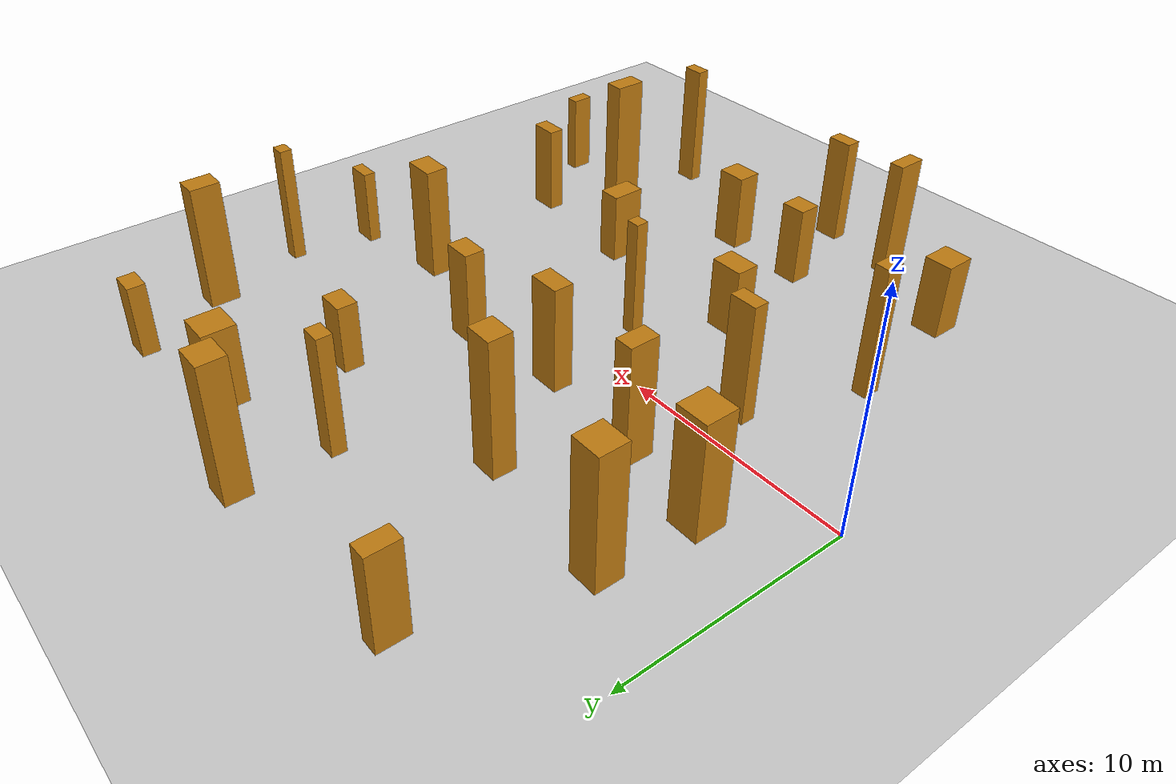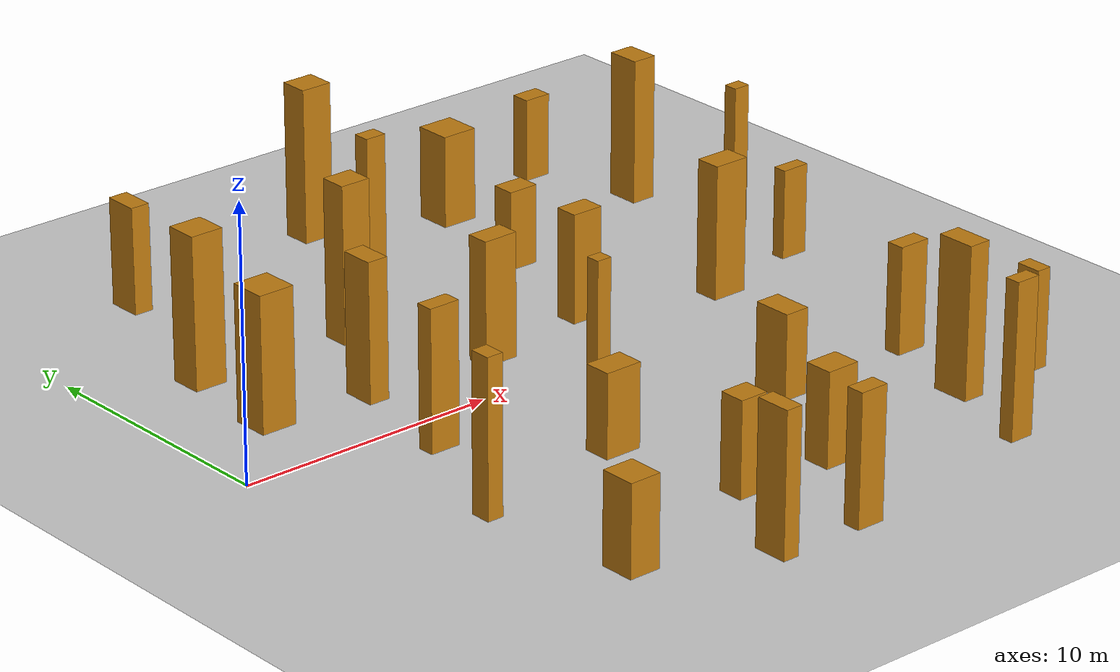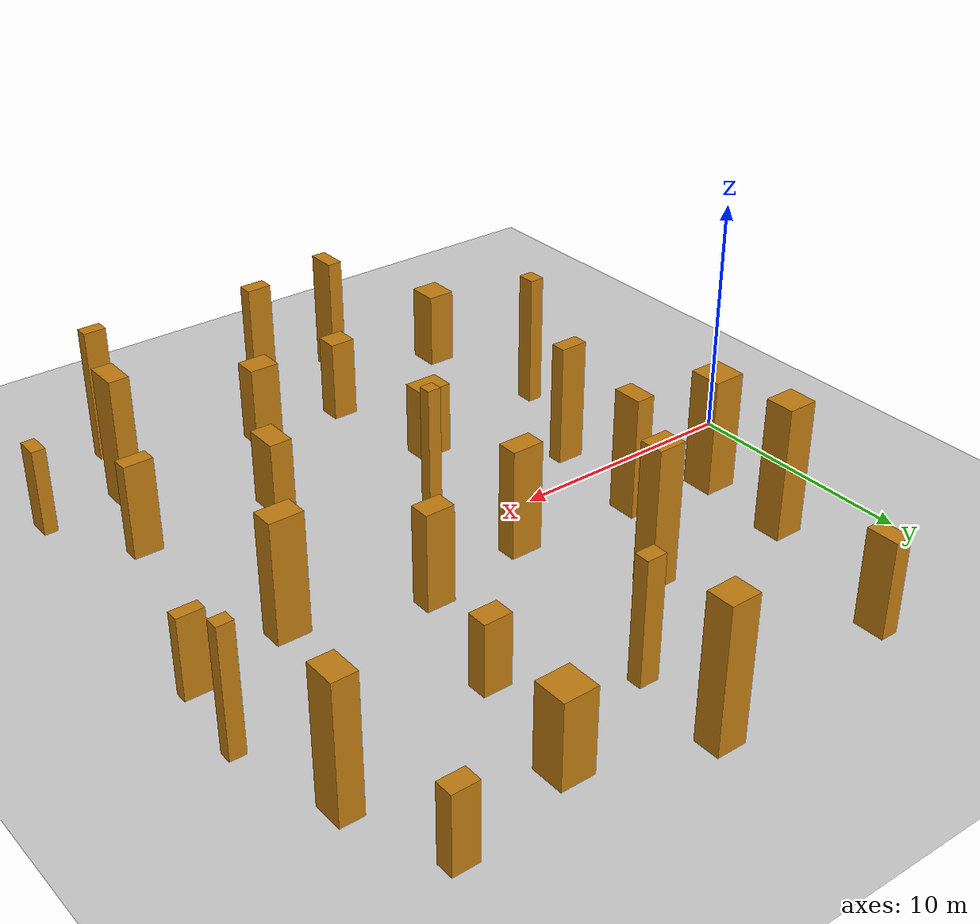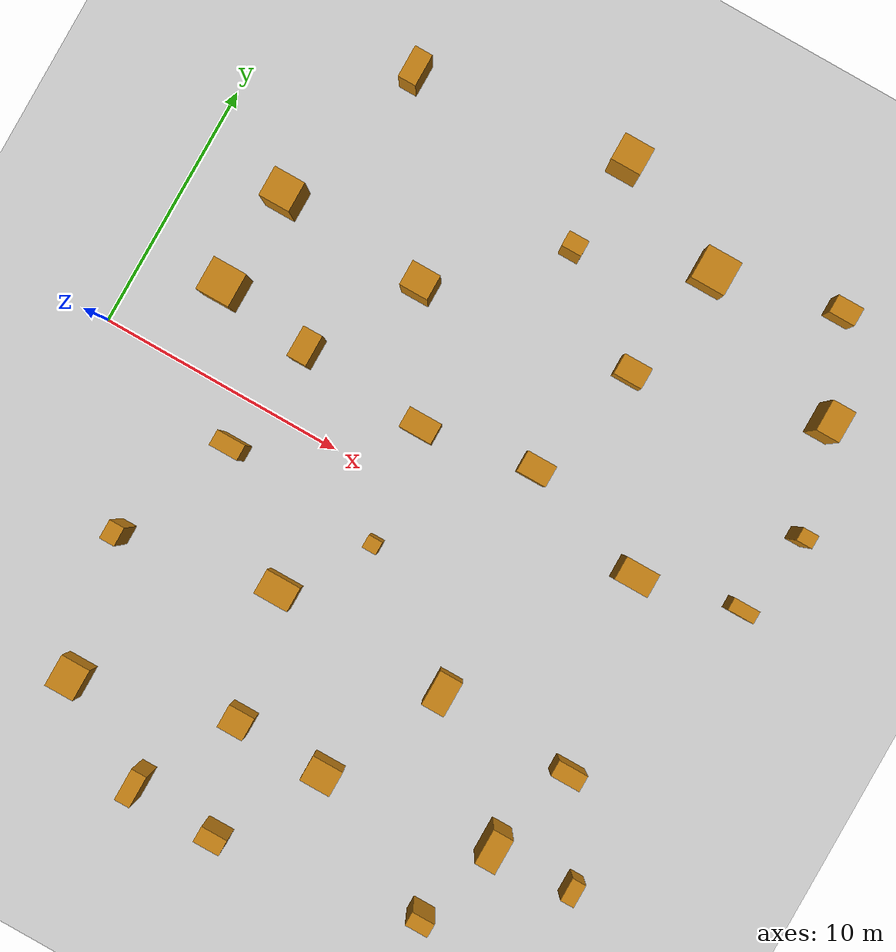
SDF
<sdf version="1.7">
 <world name="default">
  <light name="sun" type="directional">
   <pose>0 0 10 0 -0 0</pose>
   <diffuse>0.8 0.8 0.8 1</diffuse>
   <specular>0.2 0.2 0.2 1</specular>
   <attenuation>
    <range>1000</range>
    <constant>0.9</constant>
    <linear>0.01</linear>
    <quadratic>0.001</quadratic>
   </attenuation>
   <direction>-0.5 0.1 -0.9</direction>
   <spot><inner_angle>0</inner_angle><outer_angle>0</outer_angle><falloff>0</falloff></spot>
  </light>
  <model name="ground_plane">
   <static>1</static>
   <link name="link">
    <collision name="collision">
     <geometry><plane><normal>0 0 1</normal><size>100 100</size></plane></geometry>
     <surface>
      <contact><collide_bitmask>65535</collide_bitmask></contact>
      <friction><ode><mu>100</mu><mu2>50</mu2></ode></friction>
     </surface>
    </collision>
    <visual name="visual">
     <cast_shadows>0</cast_shadows>
     <geometry><plane><normal>0 0 1</normal><size>100 100</size></plane></geometry>
     <material>
      <script><uri>file://media/materials/scripts/gazebo.material</uri><name>Gazebo/Grey</name></script>
     </material>
    </visual>
   </link>
  </model>
  <gravity>0 0 -9.8</gravity>
  <magnetic_field>6e-06 2.3e-05 -4.2e-05</magnetic_field>
  <atmosphere type="adiabatic"/>
  <physics type="ode">
   <max_step_size>0.001</max_step_size>
   <real_time_factor>1</real_time_factor>
   <real_time_update_rate>1000</real_time_update_rate>
  </physics>
  <scene><ambient>0.4 0.4 0.4 1</ambient><background>0.7 0.7 0.7 1</background><shadows>1</shadows></scene>
  <spherical_coordinates>
   <surface_model>EARTH_WGS84</surface_model>
   <latitude_deg>0</latitude_deg>
   <longitude_deg>0</longitude_deg>
   <elevation>0</elevation>
   <heading_deg>0</heading_deg>
  </spherical_coordinates>
  <plugin name="gazebo_octomap" filename="libBuildOctomapPlugin.so"/>
  <model name="model0">
   <link name="link">
    <inertial>
     <mass>1</mass>
     <inertia>
      <ixx>0.166667</ixx>
      <ixy>0</ixy>
      <ixz>0</ixz>
      <iyy>0.166667</iyy>
      <iyz>0</iyz>
      <izz>0.166667</izz>
     </inertia>
    </inertial>
    <visual name="visual">
     <geometry><box><size>0.6597966464865729 0.5433565334158762 5.326100559477567</size></box></geometry>
     <material>
      <script><name>Gazebo/Grey</name><uri>file://media/materials/scripts/gazebo.material</uri></script>
      <shader type="pixel"><normal_map>__default__</normal_map></shader>
      <ambient>0.757 0.49 0.067 1</ambient>
      <diffuse>0.7 0.7 0.7 1</diffuse>
      <specular>0.01 0.01 0.01 1</specular>
      <emissive>0 0 0 1</emissive>
     </material>
    </visual>
    <collision name="collision">
     <geometry><box><size>0.6597966464865729 0.5433565334158762 5.326100559477567</size></box></geometry>
     <surface>
      <friction>
       <ode><mu>1</mu><mu2>1</mu2><fdir1>0 0 0</fdir1><slip1>0</slip1><slip2>0</slip2></ode>
       <torsional>
        <coefficient>1</coefficient>
        <patch_radius>0</patch_radius>
        <surface_radius>0</surface_radius>
        <use_patch_radius>1</use_patch_radius>
        <ode><slip>0</slip></ode>
       </torsional>
      </friction>
      <bounce><restitution_coefficient>0</restitution_coefficient><threshold>1e+06</threshold></bounce>
      <contact>
       <collide_without_contact>0</collide_without_contact>
       <collide_without_contact_bitmask>1</collide_without_contact_bitmask>
       <collide_bitmask>1</collide_bitmask>
       <ode>
        <soft_cfm>0</soft_cfm>
        <soft_erp>0.2</soft_erp>
        <kp>1e+13</kp>
        <kd>1</kd>
        <max_vel>0.01</max_vel>
        <min_depth>0</min_depth>
       </ode>
       <bullet>
        <split_impulse>1</split_impulse>
        <split_impulse_penetration_threshold>-0.01</split_impulse_penetration_threshold>
        <soft_cfm>0</soft_cfm>
        <soft_erp>0.2</soft_erp>
        <kp>1e+13</kp>
        <kd>1</kd>
       </bullet>
      </contact>
     </surface>
    </collision>
   </link>
   <static>0</static>
   <pose>26.97412062747795 5.797697109522776 2.6630502797387834 0.0 0.0 0.0</pose>
  </model>
  <model name="model1">
   <link name="link">
    <inertial>
     <mass>1</mass>
     <inertia>
      <ixx>0.166667</ixx>
      <ixy>0</ixy>
      <ixz>0</ixz>
      <iyy>0.166667</iyy>
      <iyz>0</iyz>
      <izz>0.166667</izz>
     </inertia>
    </inertial>
    <visual name="visual">
     <geometry><box><size>0.5839454857871971 0.5363072311326109 5.159209211872117</size></box></geometry>
     <material>
      <script><name>Gazebo/Grey</name><uri>file://media/materials/scripts/gazebo.material</uri></script>
      <shader type="pixel"><normal_map>__default__</normal_map></shader>
      <ambient>0.757 0.49 0.067 1</ambient>
      <diffuse>0.7 0.7 0.7 1</diffuse>
      <specular>0.01 0.01 0.01 1</specular>
      <emissive>0 0 0 1</emissive>
     </material>
    </visual>
    <collision name="collision">
     <geometry><box><size>0.5839454857871971 0.5363072311326109 5.159209211872117</size></box></geometry>
     <surface>
      <friction>
       <ode><mu>1</mu><mu2>1</mu2><fdir1>0 0 0</fdir1><slip1>0</slip1><slip2>0</slip2></ode>
       <torsional>
        <coefficient>1</coefficient>
        <patch_radius>0</patch_radius>
        <surface_radius>0</surface_radius>
        <use_patch_radius>1</use_patch_radius>
        <ode><slip>0</slip></ode>
       </torsional>
      </friction>
      <bounce><restitution_coefficient>0</restitution_coefficient><threshold>1e+06</threshold></bounce>
      <contact>
       <collide_without_contact>0</collide_without_contact>
       <collide_without_contact_bitmask>1</collide_without_contact_bitmask>
       <collide_bitmask>1</collide_bitmask>
       <ode>
        <soft_cfm>0</soft_cfm>
        <soft_erp>0.2</soft_erp>
        <kp>1e+13</kp>
        <kd>1</kd>
        <max_vel>0.01</max_vel>
        <min_depth>0</min_depth>
       </ode>
       <bullet>
        <split_impulse>1</split_impulse>
        <split_impulse_penetration_threshold>-0.01</split_impulse_penetration_threshold>
        <soft_cfm>0</soft_cfm>
        <soft_erp>0.2</soft_erp>
        <kp>1e+13</kp>
        <kd>1</kd>
       </bullet>
      </contact>
     </surface>
    </collision>
   </link>
   <static>0</static>
   <pose>13.085927521723836 -2.365363754695082 2.5796046059360584 0.0 0.0 0.0</pose>
  </model>
  <model name="model2">
   <link name="link">
    <inertial>
     <mass>1</mass>
     <inertia>
      <ixx>0.166667</ixx>
      <ixy>0</ixy>
      <ixz>0</ixz>
      <iyy>0.166667</iyy>
      <iyz>0</iyz>
      <izz>0.166667</izz>
     </inertia>
    </inertial>
    <visual name="visual">
     <geometry><box><size>1.2053655245220571 1.314765779311354 3.340665531903921</size></box></geometry>
     <material>
      <script><name>Gazebo/Grey</name><uri>file://media/materials/scripts/gazebo.material</uri></script>
      <shader type="pixel"><normal_map>__default__</normal_map></shader>
      <ambient>0.757 0.49 0.067 1</ambient>
      <diffuse>0.7 0.7 0.7 1</diffuse>
      <specular>0.01 0.01 0.01 1</specular>
      <emissive>0 0 0 1</emissive>
     </material>
    </visual>
    <collision name="collision">
     <geometry><box><size>1.2053655245220571 1.314765779311354 3.340665531903921</size></box></geometry>
     <surface>
      <friction>
       <ode><mu>1</mu><mu2>1</mu2><fdir1>0 0 0</fdir1><slip1>0</slip1><slip2>0</slip2></ode>
       <torsional>
        <coefficient>1</coefficient>
        <patch_radius>0</patch_radius>
        <surface_radius>0</surface_radius>
        <use_patch_radius>1</use_patch_radius>
        <ode><slip>0</slip></ode>
       </torsional>
      </friction>
      <bounce><restitution_coefficient>0</restitution_coefficient><threshold>1e+06</threshold></bounce>
      <contact>
       <collide_without_contact>0</collide_without_contact>
       <collide_without_contact_bitmask>1</collide_without_contact_bitmask>
       <collide_bitmask>1</collide_bitmask>
       <ode>
        <soft_cfm>0</soft_cfm>
        <soft_erp>0.2</soft_erp>
        <kp>1e+13</kp>
        <kd>1</kd>
        <max_vel>0.01</max_vel>
        <min_depth>0</min_depth>
       </ode>
       <bullet>
        <split_impulse>1</split_impulse>
        <split_impulse_penetration_threshold>-0.01</split_impulse_penetration_threshold>
        <soft_cfm>0</soft_cfm>
        <soft_erp>0.2</soft_erp>
        <kp>1e+13</kp>
        <kd>1</kd>
       </bullet>
      </contact>
     </surface>
    </collision>
   </link>
   <static>0</static>
   <pose>5.5797926981476715 -12.387064183416093 1.6703327659519605 0.0 0.0 0.0</pose>
  </model>
  <model name="model3">
   <link name="link">
    <inertial>
     <mass>1</mass>
     <inertia>
      <ixx>0.166667</ixx>
      <ixy>0</ixy>
      <ixz>0</ixz>
      <iyy>0.166667</iyy>
      <iyz>0</iyz>
      <izz>0.166667</izz>
     </inertia>
    </inertial>
    <visual name="visual">
     <geometry><box><size>1.2248682514001747 0.6664363674741199 4.035094005406677</size></box></geometry>
     <material>
      <script><name>Gazebo/Grey</name><uri>file://media/materials/scripts/gazebo.material</uri></script>
      <shader type="pixel"><normal_map>__default__</normal_map></shader>
      <ambient>0.757 0.49 0.067 1</ambient>
      <diffuse>0.7 0.7 0.7 1</diffuse>
      <specular>0.01 0.01 0.01 1</specular>
      <emissive>0 0 0 1</emissive>
     </material>
    </visual>
    <collision name="collision">
     <geometry><box><size>1.2248682514001747 0.6664363674741199 4.035094005406677</size></box></geometry>
     <surface>
      <friction>
       <ode><mu>1</mu><mu2>1</mu2><fdir1>0 0 0</fdir1><slip1>0</slip1><slip2>0</slip2></ode>
       <torsional>
        <coefficient>1</coefficient>
        <patch_radius>0</patch_radius>
        <surface_radius>0</surface_radius>
        <use_patch_radius>1</use_patch_radius>
        <ode><slip>0</slip></ode>
       </torsional>
      </friction>
      <bounce><restitution_coefficient>0</restitution_coefficient><threshold>1e+06</threshold></bounce>
      <contact>
       <collide_without_contact>0</collide_without_contact>
       <collide_without_contact_bitmask>1</collide_without_contact_bitmask>
       <collide_bitmask>1</collide_bitmask>
       <ode>
        <soft_cfm>0</soft_cfm>
        <soft_erp>0.2</soft_erp>
        <kp>1e+13</kp>
        <kd>1</kd>
        <max_vel>0.01</max_vel>
        <min_depth>0</min_depth>
       </ode>
       <bullet>
        <split_impulse>1</split_impulse>
        <split_impulse_penetration_threshold>-0.01</split_impulse_penetration_threshold>
        <soft_cfm>0</soft_cfm>
        <soft_erp>0.2</soft_erp>
        <kp>1e+13</kp>
        <kd>1</kd>
       </bullet>
      </contact>
     </surface>
    </collision>
   </link>
   <static>0</static>
   <pose>23.726230977202416 -6.264467416354764 2.0175470027033384 0.0 0.0 0.0</pose>
  </model>
  <model name="model4">
   <link name="link">
    <inertial>
     <mass>1</mass>
     <inertia>
      <ixx>0.166667</ixx>
      <ixy>0</ixy>
      <ixz>0</ixz>
      <iyy>0.166667</iyy>
      <iyz>0</iyz>
      <izz>0.166667</izz>
     </inertia>
    </inertial>
    <visual name="visual">
     <geometry><box><size>0.8350673018529385 0.6346498263390593 5.191413497331203</size></box></geometry>
     <material>
      <script><name>Gazebo/Grey</name><uri>file://media/materials/scripts/gazebo.material</uri></script>
      <shader type="pixel"><normal_map>__default__</normal_map></shader>
      <ambient>0.757 0.49 0.067 1</ambient>
      <diffuse>0.7 0.7 0.7 1</diffuse>
      <specular>0.01 0.01 0.01 1</specular>
      <emissive>0 0 0 1</emissive>
     </material>
    </visual>
    <collision name="collision">
     <geometry><box><size>0.8350673018529385 0.6346498263390593 5.191413497331203</size></box></geometry>
     <surface>
      <friction>
       <ode><mu>1</mu><mu2>1</mu2><fdir1>0 0 0</fdir1><slip1>0</slip1><slip2>0</slip2></ode>
       <torsional>
        <coefficient>1</coefficient>
        <patch_radius>0</patch_radius>
        <surface_radius>0</surface_radius>
        <use_patch_radius>1</use_patch_radius>
        <ode><slip>0</slip></ode>
       </torsional>
      </friction>
      <bounce><restitution_coefficient>0</restitution_coefficient><threshold>1e+06</threshold></bounce>
      <contact>
       <collide_without_contact>0</collide_without_contact>
       <collide_without_contact_bitmask>1</collide_without_contact_bitmask>
       <collide_bitmask>1</collide_bitmask>
       <ode>
        <soft_cfm>0</soft_cfm>
        <soft_erp>0.2</soft_erp>
        <kp>1e+13</kp>
        <kd>1</kd>
        <max_vel>0.01</max_vel>
        <min_depth>0</min_depth>
       </ode>
       <bullet>
        <split_impulse>1</split_impulse>
        <split_impulse_penetration_threshold>-0.01</split_impulse_penetration_threshold>
        <soft_cfm>0</soft_cfm>
        <soft_erp>0.2</soft_erp>
        <kp>1e+13</kp>
        <kd>1</kd>
       </bullet>
      </contact>
     </surface>
    </collision>
   </link>
   <static>0</static>
   <pose>14.127437549624553 11.041690797355706 2.5957067486656014 0.0 0.0 0.0</pose>
  </model>
  <model name="model5">
   <link name="link">
    <inertial>
     <mass>1</mass>
     <inertia>
      <ixx>0.166667</ixx>
      <ixy>0</ixy>
      <ixz>0</ixz>
      <iyy>0.166667</iyy>
      <iyz>0</iyz>
      <izz>0.166667</izz>
     </inertia>
    </inertial>
    <visual name="visual">
     <geometry><box><size>1.420351690742608 1.4059996348466806 3.5472753856791237</size></box></geometry>
     <material>
      <script><name>Gazebo/Grey</name><uri>file://media/materials/scripts/gazebo.material</uri></script>
      <shader type="pixel"><normal_map>__default__</normal_map></shader>
      <ambient>0.757 0.49 0.067 1</ambient>
      <diffuse>0.7 0.7 0.7 1</diffuse>
      <specular>0.01 0.01 0.01 1</specular>
      <emissive>0 0 0 1</emissive>
     </material>
    </visual>
    <collision name="collision">
     <geometry><box><size>1.420351690742608 1.4059996348466806 3.5472753856791237</size></box></geometry>
     <surface>
      <friction>
       <ode><mu>1</mu><mu2>1</mu2><fdir1>0 0 0</fdir1><slip1>0</slip1><slip2>0</slip2></ode>
       <torsional>
        <coefficient>1</coefficient>
        <patch_radius>0</patch_radius>
        <surface_radius>0</surface_radius>
        <use_patch_radius>1</use_patch_radius>
        <ode><slip>0</slip></ode>
       </torsional>
      </friction>
      <bounce><restitution_coefficient>0</restitution_coefficient><threshold>1e+06</threshold></bounce>
      <contact>
       <collide_without_contact>0</collide_without_contact>
       <collide_without_contact_bitmask>1</collide_without_contact_bitmask>
       <collide_bitmask>1</collide_bitmask>
       <ode>
        <soft_cfm>0</soft_cfm>
        <soft_erp>0.2</soft_erp>
        <kp>1e+13</kp>
        <kd>1</kd>
        <max_vel>0.01</max_vel>
        <min_depth>0</min_depth>
       </ode>
       <bullet>
        <split_impulse>1</split_impulse>
        <split_impulse_penetration_threshold>-0.01</split_impulse_penetration_threshold>
        <soft_cfm>0</soft_cfm>
        <soft_erp>0.2</soft_erp>
        <kp>1e+13</kp>
        <kd>1</kd>
       </bullet>
      </contact>
     </surface>
    </collision>
   </link>
   <static>0</static>
   <pose>19.210867779731654 12.896892039692435 1.7736376928395619 0.0 0.0 0.0</pose>
  </model>
  <model name="model6">
   <link name="link">
    <inertial>
     <mass>1</mass>
     <inertia>
      <ixx>0.166667</ixx>
      <ixy>0</ixy>
      <ixz>0</ixz>
      <iyy>0.166667</iyy>
      <iyz>0</iyz>
      <izz>0.166667</izz>
     </inertia>
    </inertial>
    <visual name="visual">
     <geometry><box><size>0.8510653237710026 1.4387723617051402 5.681280423808036</size></box></geometry>
     <material>
      <script><name>Gazebo/Grey</name><uri>file://media/materials/scripts/gazebo.material</uri></script>
      <shader type="pixel"><normal_map>__default__</normal_map></shader>
      <ambient>0.757 0.49 0.067 1</ambient>
      <diffuse>0.7 0.7 0.7 1</diffuse>
      <specular>0.01 0.01 0.01 1</specular>
      <emissive>0 0 0 1</emissive>
     </material>
    </visual>
    <collision name="collision">
     <geometry><box><size>0.8510653237710026 1.4387723617051402 5.681280423808036</size></box></geometry>
     <surface>
      <friction>
       <ode><mu>1</mu><mu2>1</mu2><fdir1>0 0 0</fdir1><slip1>0</slip1><slip2>0</slip2></ode>
       <torsional>
        <coefficient>1</coefficient>
        <patch_radius>0</patch_radius>
        <surface_radius>0</surface_radius>
        <use_patch_radius>1</use_patch_radius>
        <ode><slip>0</slip></ode>
       </torsional>
      </friction>
      <bounce><restitution_coefficient>0</restitution_coefficient><threshold>1e+06</threshold></bounce>
      <contact>
       <collide_without_contact>0</collide_without_contact>
       <collide_without_contact_bitmask>1</collide_without_contact_bitmask>
       <collide_bitmask>1</collide_bitmask>
       <ode>
        <soft_cfm>0</soft_cfm>
        <soft_erp>0.2</soft_erp>
        <kp>1e+13</kp>
        <kd>1</kd>
        <max_vel>0.01</max_vel>
        <min_depth>0</min_depth>
       </ode>
       <bullet>
        <split_impulse>1</split_impulse>
        <split_impulse_penetration_threshold>-0.01</split_impulse_penetration_threshold>
        <soft_cfm>0</soft_cfm>
        <soft_erp>0.2</soft_erp>
        <kp>1e+13</kp>
        <kd>1</kd>
       </bullet>
      </contact>
     </surface>
    </collision>
   </link>
   <static>0</static>
   <pose>22.594056254561426 -9.98770469466633 2.840640211904018 0.0 0.0 0.0</pose>
  </model>
  <model name="model7">
   <link name="link">
    <inertial>
     <mass>1</mass>
     <inertia>
      <ixx>0.166667</ixx>
      <ixy>0</ixy>
      <ixz>0</ixz>
      <iyy>0.166667</iyy>
      <iyz>0</iyz>
      <izz>0.166667</izz>
     </inertia>
    </inertial>
    <visual name="visual">
     <geometry><box><size>1.3609990061537673 0.8579866355465122 4.659966668525682</size></box></geometry>
     <material>
      <script><name>Gazebo/Grey</name><uri>file://media/materials/scripts/gazebo.material</uri></script>
      <shader type="pixel"><normal_map>__default__</normal_map></shader>
      <ambient>0.757 0.49 0.067 1</ambient>
      <diffuse>0.7 0.7 0.7 1</diffuse>
      <specular>0.01 0.01 0.01 1</specular>
      <emissive>0 0 0 1</emissive>
     </material>
    </visual>
    <collision name="collision">
     <geometry><box><size>1.3609990061537673 0.8579866355465122 4.659966668525682</size></box></geometry>
     <surface>
      <friction>
       <ode><mu>1</mu><mu2>1</mu2><fdir1>0 0 0</fdir1><slip1>0</slip1><slip2>0</slip2></ode>
       <torsional>
        <coefficient>1</coefficient>
        <patch_radius>0</patch_radius>
        <surface_radius>0</surface_radius>
        <use_patch_radius>1</use_patch_radius>
        <ode><slip>0</slip></ode>
       </torsional>
      </friction>
      <bounce><restitution_coefficient>0</restitution_coefficient><threshold>1e+06</threshold></bounce>
      <contact>
       <collide_without_contact>0</collide_without_contact>
       <collide_without_contact_bitmask>1</collide_without_contact_bitmask>
       <collide_bitmask>1</collide_bitmask>
       <ode>
        <soft_cfm>0</soft_cfm>
        <soft_erp>0.2</soft_erp>
        <kp>1e+13</kp>
        <kd>1</kd>
        <max_vel>0.01</max_vel>
        <min_depth>0</min_depth>
       </ode>
       <bullet>
        <split_impulse>1</split_impulse>
        <split_impulse_penetration_threshold>-0.01</split_impulse_penetration_threshold>
        <soft_cfm>0</soft_cfm>
        <soft_erp>0.2</soft_erp>
        <kp>1e+13</kp>
        <kd>1</kd>
       </bullet>
      </contact>
     </surface>
    </collision>
   </link>
   <static>0</static>
   <pose>12.444823412982197 2.362173613408313 2.329983334262841 0.0 0.0 0.0</pose>
  </model>
  <model name="model8">
   <link name="link">
    <inertial>
     <mass>1</mass>
     <inertia>
      <ixx>0.166667</ixx>
      <ixy>0</ixy>
      <ixz>0</ixz>
      <iyy>0.166667</iyy>
      <iyz>0</iyz>
      <izz>0.166667</izz>
     </inertia>
    </inertial>
    <visual name="visual">
     <geometry><box><size>1.39973562247595 0.9698481885303738 5.084058155108195</size></box></geometry>
     <material>
      <script><name>Gazebo/Grey</name><uri>file://media/materials/scripts/gazebo.material</uri></script>
      <shader type="pixel"><normal_map>__default__</normal_map></shader>
      <ambient>0.757 0.49 0.067 1</ambient>
      <diffuse>0.7 0.7 0.7 1</diffuse>
      <specular>0.01 0.01 0.01 1</specular>
      <emissive>0 0 0 1</emissive>
     </material>
    </visual>
    <collision name="collision">
     <geometry><box><size>1.39973562247595 0.9698481885303738 5.084058155108195</size></box></geometry>
     <surface>
      <friction>
       <ode><mu>1</mu><mu2>1</mu2><fdir1>0 0 0</fdir1><slip1>0</slip1><slip2>0</slip2></ode>
       <torsional>
        <coefficient>1</coefficient>
        <patch_radius>0</patch_radius>
        <surface_radius>0</surface_radius>
        <use_patch_radius>1</use_patch_radius>
        <ode><slip>0</slip></ode>
       </torsional>
      </friction>
      <bounce><restitution_coefficient>0</restitution_coefficient><threshold>1e+06</threshold></bounce>
      <contact>
       <collide_without_contact>0</collide_without_contact>
       <collide_without_contact_bitmask>1</collide_without_contact_bitmask>
       <collide_bitmask>1</collide_bitmask>
       <ode>
        <soft_cfm>0</soft_cfm>
        <soft_erp>0.2</soft_erp>
        <kp>1e+13</kp>
        <kd>1</kd>
        <max_vel>0.01</max_vel>
        <min_depth>0</min_depth>
       </ode>
       <bullet>
        <split_impulse>1</split_impulse>
        <split_impulse_penetration_threshold>-0.01</split_impulse_penetration_threshold>
        <soft_cfm>0</soft_cfm>
        <soft_erp>0.2</soft_erp>
        <kp>1e+13</kp>
        <kd>1</kd>
       </bullet>
      </contact>
     </surface>
    </collision>
   </link>
   <static>0</static>
   <pose>22.21596540278362 1.4348585282058508 2.5420290775540977 0.0 0.0 0.0</pose>
  </model>
  <model name="model9">
   <link name="link">
    <inertial>
     <mass>1</mass>
     <inertia>
      <ixx>0.166667</ixx>
      <ixy>0</ixy>
      <ixz>0</ixz>
      <iyy>0.166667</iyy>
      <iyz>0</iyz>
      <izz>0.166667</izz>
     </inertia>
    </inertial>
    <visual name="visual">
     <geometry><box><size>0.5692556528215651 0.9577031488105343 3.702021957161678</size></box></geometry>
     <material>
      <script><name>Gazebo/Grey</name><uri>file://media/materials/scripts/gazebo.material</uri></script>
      <shader type="pixel"><normal_map>__default__</normal_map></shader>
      <ambient>0.757 0.49 0.067 1</ambient>
      <diffuse>0.7 0.7 0.7 1</diffuse>
      <specular>0.01 0.01 0.01 1</specular>
      <emissive>0 0 0 1</emissive>
     </material>
    </visual>
    <collision name="collision">
     <geometry><box><size>0.5692556528215651 0.9577031488105343 3.702021957161678</size></box></geometry>
     <surface>
      <friction>
       <ode><mu>1</mu><mu2>1</mu2><fdir1>0 0 0</fdir1><slip1>0</slip1><slip2>0</slip2></ode>
       <torsional>
        <coefficient>1</coefficient>
        <patch_radius>0</patch_radius>
        <surface_radius>0</surface_radius>
        <use_patch_radius>1</use_patch_radius>
        <ode><slip>0</slip></ode>
       </torsional>
      </friction>
      <bounce><restitution_coefficient>0</restitution_coefficient><threshold>1e+06</threshold></bounce>
      <contact>
       <collide_without_contact>0</collide_without_contact>
       <collide_without_contact_bitmask>1</collide_without_contact_bitmask>
       <collide_bitmask>1</collide_bitmask>
       <ode>
        <soft_cfm>0</soft_cfm>
        <soft_erp>0.2</soft_erp>
        <kp>1e+13</kp>
        <kd>1</kd>
        <max_vel>0.01</max_vel>
        <min_depth>0</min_depth>
       </ode>
       <bullet>
        <split_impulse>1</split_impulse>
        <split_impulse_penetration_threshold>-0.01</split_impulse_penetration_threshold>
        <soft_cfm>0</soft_cfm>
        <soft_erp>0.2</soft_erp>
        <kp>1e+13</kp>
        <kd>1</kd>
       </bullet>
      </contact>
     </surface>
    </collision>
   </link>
   <static>0</static>
   <pose>26.026751026869118 -10.01202915709383 1.851010978580839 0.0 0.0 0.0</pose>
  </model>
  <model name="model10">
   <link name="link">
    <inertial>
     <mass>1</mass>
     <inertia>
      <ixx>0.166667</ixx>
      <ixy>0</ixy>
      <ixz>0</ixz>
      <iyy>0.166667</iyy>
      <iyz>0</iyz>
      <izz>0.166667</izz>
     </inertia>
    </inertial>
    <visual name="visual">
     <geometry><box><size>1.440011845833056 1.0309240658905319 3.1242760051178307</size></box></geometry>
     <material>
      <script><name>Gazebo/Grey</name><uri>file://media/materials/scripts/gazebo.material</uri></script>
      <shader type="pixel"><normal_map>__default__</normal_map></shader>
      <ambient>0.757 0.49 0.067 1</ambient>
      <diffuse>0.7 0.7 0.7 1</diffuse>
      <specular>0.01 0.01 0.01 1</specular>
      <emissive>0 0 0 1</emissive>
     </material>
    </visual>
    <collision name="collision">
     <geometry><box><size>1.440011845833056 1.0309240658905319 3.1242760051178307</size></box></geometry>
     <surface>
      <friction>
       <ode><mu>1</mu><mu2>1</mu2><fdir1>0 0 0</fdir1><slip1>0</slip1><slip2>0</slip2></ode>
       <torsional>
        <coefficient>1</coefficient>
        <patch_radius>0</patch_radius>
        <surface_radius>0</surface_radius>
        <use_patch_radius>1</use_patch_radius>
        <ode><slip>0</slip></ode>
       </torsional>
      </friction>
      <bounce><restitution_coefficient>0</restitution_coefficient><threshold>1e+06</threshold></bounce>
      <contact>
       <collide_without_contact>0</collide_without_contact>
       <collide_without_contact_bitmask>1</collide_without_contact_bitmask>
       <collide_bitmask>1</collide_bitmask>
       <ode>
        <soft_cfm>0</soft_cfm>
        <soft_erp>0.2</soft_erp>
        <kp>1e+13</kp>
        <kd>1</kd>
        <max_vel>0.01</max_vel>
        <min_depth>0</min_depth>
       </ode>
       <bullet>
        <split_impulse>1</split_impulse>
        <split_impulse_penetration_threshold>-0.01</split_impulse_penetration_threshold>
        <soft_cfm>0</soft_cfm>
        <soft_erp>0.2</soft_erp>
        <kp>1e+13</kp>
        <kd>1</kd>
       </bullet>
      </contact>
     </surface>
    </collision>
   </link>
   <static>0</static>
   <pose>10.8000576414267 -5.675402770973076 1.5621380025589153 0.0 0.0 0.0</pose>
  </model>
  <model name="model11">
   <link name="link">
    <inertial>
     <mass>1</mass>
     <inertia>
      <ixx>0.166667</ixx>
      <ixy>0</ixy>
      <ixz>0</ixz>
      <iyy>0.166667</iyy>
      <iyz>0</iyz>
      <izz>0.166667</izz>
     </inertia>
    </inertial>
    <visual name="visual">
     <geometry><box><size>0.7419718425151329 1.311030205805578 4.057804555854417</size></box></geometry>
     <material>
      <script><name>Gazebo/Grey</name><uri>file://media/materials/scripts/gazebo.material</uri></script>
      <shader type="pixel"><normal_map>__default__</normal_map></shader>
      <ambient>0.757 0.49 0.067 1</ambient>
      <diffuse>0.7 0.7 0.7 1</diffuse>
      <specular>0.01 0.01 0.01 1</specular>
      <emissive>0 0 0 1</emissive>
     </material>
    </visual>
    <collision name="collision">
     <geometry><box><size>0.7419718425151329 1.311030205805578 4.057804555854417</size></box></geometry>
     <surface>
      <friction>
       <ode><mu>1</mu><mu2>1</mu2><fdir1>0 0 0</fdir1><slip1>0</slip1><slip2>0</slip2></ode>
       <torsional>
        <coefficient>1</coefficient>
        <patch_radius>0</patch_radius>
        <surface_radius>0</surface_radius>
        <use_patch_radius>1</use_patch_radius>
        <ode><slip>0</slip></ode>
       </torsional>
      </friction>
      <bounce><restitution_coefficient>0</restitution_coefficient><threshold>1e+06</threshold></bounce>
      <contact>
       <collide_without_contact>0</collide_without_contact>
       <collide_without_contact_bitmask>1</collide_without_contact_bitmask>
       <collide_bitmask>1</collide_bitmask>
       <ode>
        <soft_cfm>0</soft_cfm>
        <soft_erp>0.2</soft_erp>
        <kp>1e+13</kp>
        <kd>1</kd>
        <max_vel>0.01</max_vel>
        <min_depth>0</min_depth>
       </ode>
       <bullet>
        <split_impulse>1</split_impulse>
        <split_impulse_penetration_threshold>-0.01</split_impulse_penetration_threshold>
        <soft_cfm>0</soft_cfm>
        <soft_erp>0.2</soft_erp>
        <kp>1e+13</kp>
        <kd>1</kd>
       </bullet>
      </contact>
     </surface>
    </collision>
   </link>
   <static>0</static>
   <pose>5.656998009752081 13.93431440700892 2.0289022779272083 0.0 0.0 0.0</pose>
  </model>
  <model name="model12">
   <link name="link">
    <inertial>
     <mass>1</mass>
     <inertia>
      <ixx>0.166667</ixx>
      <ixy>0</ixy>
      <ixz>0</ixz>
      <iyy>0.166667</iyy>
      <iyz>0</iyz>
      <izz>0.166667</izz>
     </inertia>
    </inertial>
    <visual name="visual">
     <geometry><box><size>0.945465766151815 0.5612854688396307 5.777602081277838</size></box></geometry>
     <material>
      <script><name>Gazebo/Grey</name><uri>file://media/materials/scripts/gazebo.material</uri></script>
      <shader type="pixel"><normal_map>__default__</normal_map></shader>
      <ambient>0.757 0.49 0.067 1</ambient>
      <diffuse>0.7 0.7 0.7 1</diffuse>
      <specular>0.01 0.01 0.01 1</specular>
      <emissive>0 0 0 1</emissive>
     </material>
    </visual>
    <collision name="collision">
     <geometry><box><size>0.945465766151815 0.5612854688396307 5.777602081277838</size></box></geometry>
     <surface>
      <friction>
       <ode><mu>1</mu><mu2>1</mu2><fdir1>0 0 0</fdir1><slip1>0</slip1><slip2>0</slip2></ode>
       <torsional>
        <coefficient>1</coefficient>
        <patch_radius>0</patch_radius>
        <surface_radius>0</surface_radius>
        <use_patch_radius>1</use_patch_radius>
        <ode><slip>0</slip></ode>
       </torsional>
      </friction>
      <bounce><restitution_coefficient>0</restitution_coefficient><threshold>1e+06</threshold></bounce>
      <contact>
       <collide_without_contact>0</collide_without_contact>
       <collide_without_contact_bitmask>1</collide_without_contact_bitmask>
       <collide_bitmask>1</collide_bitmask>
       <ode>
        <soft_cfm>0</soft_cfm>
        <soft_erp>0.2</soft_erp>
        <kp>1e+13</kp>
        <kd>1</kd>
        <max_vel>0.01</max_vel>
        <min_depth>0</min_depth>
       </ode>
       <bullet>
        <split_impulse>1</split_impulse>
        <split_impulse_penetration_threshold>-0.01</split_impulse_penetration_threshold>
        <soft_cfm>0</soft_cfm>
        <soft_erp>0.2</soft_erp>
        <kp>1e+13</kp>
        <kd>1</kd>
       </bullet>
      </contact>
     </surface>
    </collision>
   </link>
   <static>0</static>
   <pose>21.523943800142888 -13.661303301543098 2.888801040638919 0.0 0.0 0.0</pose>
  </model>
  <model name="model13">
   <link name="link">
    <inertial>
     <mass>1</mass>
     <inertia>
      <ixx>0.166667</ixx>
      <ixy>0</ixy>
      <ixz>0</ixz>
      <iyy>0.166667</iyy>
      <iyz>0</iyz>
      <izz>0.166667</izz>
     </inertia>
    </inertial>
    <visual name="visual">
     <geometry><box><size>0.9709278101786866 1.283737654702767 5.597132644336313</size></box></geometry>
     <material>
      <script><name>Gazebo/Grey</name><uri>file://media/materials/scripts/gazebo.material</uri></script>
      <shader type="pixel"><normal_map>__default__</normal_map></shader>
      <ambient>0.757 0.49 0.067 1</ambient>
      <diffuse>0.7 0.7 0.7 1</diffuse>
      <specular>0.01 0.01 0.01 1</specular>
      <emissive>0 0 0 1</emissive>
     </material>
    </visual>
    <collision name="collision">
     <geometry><box><size>0.9709278101786866 1.283737654702767 5.597132644336313</size></box></geometry>
     <surface>
      <friction>
       <ode><mu>1</mu><mu2>1</mu2><fdir1>0 0 0</fdir1><slip1>0</slip1><slip2>0</slip2></ode>
       <torsional>
        <coefficient>1</coefficient>
        <patch_radius>0</patch_radius>
        <surface_radius>0</surface_radius>
        <use_patch_radius>1</use_patch_radius>
        <ode><slip>0</slip></ode>
       </torsional>
      </friction>
      <bounce><restitution_coefficient>0</restitution_coefficient><threshold>1e+06</threshold></bounce>
      <contact>
       <collide_without_contact>0</collide_without_contact>
       <collide_without_contact_bitmask>1</collide_without_contact_bitmask>
       <collide_bitmask>1</collide_bitmask>
       <ode>
        <soft_cfm>0</soft_cfm>
        <soft_erp>0.2</soft_erp>
        <kp>1e+13</kp>
        <kd>1</kd>
        <max_vel>0.01</max_vel>
        <min_depth>0</min_depth>
       </ode>
       <bullet>
        <split_impulse>1</split_impulse>
        <split_impulse_penetration_threshold>-0.01</split_impulse_penetration_threshold>
        <soft_cfm>0</soft_cfm>
        <soft_erp>0.2</soft_erp>
        <kp>1e+13</kp>
        <kd>1</kd>
       </bullet>
      </contact>
     </surface>
    </collision>
   </link>
   <static>0</static>
   <pose>25.737608231872454 10.061197598316717 2.7985663221681567 0.0 0.0 0.0</pose>
  </model>
  <model name="model14">
   <link name="link">
    <inertial>
     <mass>1</mass>
     <inertia>
      <ixx>0.166667</ixx>
      <ixy>0</ixy>
      <ixz>0</ixz>
      <iyy>0.166667</iyy>
      <iyz>0</iyz>
      <izz>0.166667</izz>
     </inertia>
    </inertial>
    <visual name="visual">
     <geometry><box><size>1.085612645199187 0.7459505998726893 3.2203096250966006</size></box></geometry>
     <material>
      <script><name>Gazebo/Grey</name><uri>file://media/materials/scripts/gazebo.material</uri></script>
      <shader type="pixel"><normal_map>__default__</normal_map></shader>
      <ambient>0.757 0.49 0.067 1</ambient>
      <diffuse>0.7 0.7 0.7 1</diffuse>
      <specular>0.01 0.01 0.01 1</specular>
      <emissive>0 0 0 1</emissive>
     </material>
    </visual>
    <collision name="collision">
     <geometry><box><size>1.085612645199187 0.7459505998726893 3.2203096250966006</size></box></geometry>
     <surface>
      <friction>
       <ode><mu>1</mu><mu2>1</mu2><fdir1>0 0 0</fdir1><slip1>0</slip1><slip2>0</slip2></ode>
       <torsional>
        <coefficient>1</coefficient>
        <patch_radius>0</patch_radius>
        <surface_radius>0</surface_radius>
        <use_patch_radius>1</use_patch_radius>
        <ode><slip>0</slip></ode>
       </torsional>
      </friction>
      <bounce><restitution_coefficient>0</restitution_coefficient><threshold>1e+06</threshold></bounce>
      <contact>
       <collide_without_contact>0</collide_without_contact>
       <collide_without_contact_bitmask>1</collide_without_contact_bitmask>
       <collide_bitmask>1</collide_bitmask>
       <ode>
        <soft_cfm>0</soft_cfm>
        <soft_erp>0.2</soft_erp>
        <kp>1e+13</kp>
        <kd>1</kd>
        <max_vel>0.01</max_vel>
        <min_depth>0</min_depth>
       </ode>
       <bullet>
        <split_impulse>1</split_impulse>
        <split_impulse_penetration_threshold>-0.01</split_impulse_penetration_threshold>
        <soft_cfm>0</soft_cfm>
        <soft_erp>0.2</soft_erp>
        <kp>1e+13</kp>
        <kd>1</kd>
       </bullet>
      </contact>
     </surface>
    </collision>
   </link>
   <static>0</static>
   <pose>24.208528531126774 14.016378220542073 1.6101548125483003 0.0 0.0 0.0</pose>
  </model>
  <model name="model15">
   <link name="link">
    <inertial>
     <mass>1</mass>
     <inertia>
      <ixx>0.166667</ixx>
      <ixy>0</ixy>
      <ixz>0</ixz>
      <iyy>0.166667</iyy>
      <iyz>0</iyz>
      <izz>0.166667</izz>
     </inertia>
    </inertial>
    <visual name="visual">
     <geometry><box><size>1.0839174982062698 0.9628404211382068 3.5362903949187983</size></box></geometry>
     <material>
      <script><name>Gazebo/Grey</name><uri>file://media/materials/scripts/gazebo.material</uri></script>
      <shader type="pixel"><normal_map>__default__</normal_map></shader>
      <ambient>0.757 0.49 0.067 1</ambient>
      <diffuse>0.7 0.7 0.7 1</diffuse>
      <specular>0.01 0.01 0.01 1</specular>
      <emissive>0 0 0 1</emissive>
     </material>
    </visual>
    <collision name="collision">
     <geometry><box><size>1.0839174982062698 0.9628404211382068 3.5362903949187983</size></box></geometry>
     <surface>
      <friction>
       <ode><mu>1</mu><mu2>1</mu2><fdir1>0 0 0</fdir1><slip1>0</slip1><slip2>0</slip2></ode>
       <torsional>
        <coefficient>1</coefficient>
        <patch_radius>0</patch_radius>
        <surface_radius>0</surface_radius>
        <use_patch_radius>1</use_patch_radius>
        <ode><slip>0</slip></ode>
       </torsional>
      </friction>
      <bounce><restitution_coefficient>0</restitution_coefficient><threshold>1e+06</threshold></bounce>
      <contact>
       <collide_without_contact>0</collide_without_contact>
       <collide_without_contact_bitmask>1</collide_without_contact_bitmask>
       <collide_bitmask>1</collide_bitmask>
       <ode>
        <soft_cfm>0</soft_cfm>
        <soft_erp>0.2</soft_erp>
        <kp>1e+13</kp>
        <kd>1</kd>
        <max_vel>0.01</max_vel>
        <min_depth>0</min_depth>
       </ode>
       <bullet>
        <split_impulse>1</split_impulse>
        <split_impulse_penetration_threshold>-0.01</split_impulse_penetration_threshold>
        <soft_cfm>0</soft_cfm>
        <soft_erp>0.2</soft_erp>
        <kp>1e+13</kp>
        <kd>1</kd>
       </bullet>
      </contact>
     </surface>
    </collision>
   </link>
   <static>0</static>
   <pose>11.907492524595437 -10.718669321916789 1.7681451974593991 0.0 0.0 0.0</pose>
  </model>
  <model name="model16">
   <link name="link">
    <inertial>
     <mass>1</mass>
     <inertia>
      <ixx>0.166667</ixx>
      <ixy>0</ixy>
      <ixz>0</ixz>
      <iyy>0.166667</iyy>
      <iyz>0</iyz>
      <izz>0.166667</izz>
     </inertia>
    </inertial>
    <visual name="visual">
     <geometry><box><size>0.9630539420621266 1.4653732134798219 3.181129588769163</size></box></geometry>
     <material>
      <script><name>Gazebo/Grey</name><uri>file://media/materials/scripts/gazebo.material</uri></script>
      <shader type="pixel"><normal_map>__default__</normal_map></shader>
      <ambient>0.757 0.49 0.067 1</ambient>
      <diffuse>0.7 0.7 0.7 1</diffuse>
      <specular>0.01 0.01 0.01 1</specular>
      <emissive>0 0 0 1</emissive>
     </material>
    </visual>
    <collision name="collision">
     <geometry><box><size>0.9630539420621266 1.4653732134798219 3.181129588769163</size></box></geometry>
     <surface>
      <friction>
       <ode><mu>1</mu><mu2>1</mu2><fdir1>0 0 0</fdir1><slip1>0</slip1><slip2>0</slip2></ode>
       <torsional>
        <coefficient>1</coefficient>
        <patch_radius>0</patch_radius>
        <surface_radius>0</surface_radius>
        <use_patch_radius>1</use_patch_radius>
        <ode><slip>0</slip></ode>
       </torsional>
      </friction>
      <bounce><restitution_coefficient>0</restitution_coefficient><threshold>1e+06</threshold></bounce>
      <contact>
       <collide_without_contact>0</collide_without_contact>
       <collide_without_contact_bitmask>1</collide_without_contact_bitmask>
       <collide_bitmask>1</collide_bitmask>
       <ode>
        <soft_cfm>0</soft_cfm>
        <soft_erp>0.2</soft_erp>
        <kp>1e+13</kp>
        <kd>1</kd>
        <max_vel>0.01</max_vel>
        <min_depth>0</min_depth>
       </ode>
       <bullet>
        <split_impulse>1</split_impulse>
        <split_impulse_penetration_threshold>-0.01</split_impulse_penetration_threshold>
        <soft_cfm>0</soft_cfm>
        <soft_erp>0.2</soft_erp>
        <kp>1e+13</kp>
        <kd>1</kd>
       </bullet>
      </contact>
     </surface>
    </collision>
   </link>
   <static>0</static>
   <pose>18.105031352682804 -5.983778802928608 1.5905647943845815 0.0 0.0 0.0</pose>
  </model>
  <model name="model17">
   <link name="link">
    <inertial>
     <mass>1</mass>
     <inertia>
      <ixx>0.166667</ixx>
      <ixy>0</ixy>
      <ixz>0</ixz>
      <iyy>0.166667</iyy>
      <iyz>0</iyz>
      <izz>0.166667</izz>
     </inertia>
    </inertial>
    <visual name="visual">
     <geometry><box><size>1.2372976752447358 1.1043510471709674 5.954559431864228</size></box></geometry>
     <material>
      <script><name>Gazebo/Grey</name><uri>file://media/materials/scripts/gazebo.material</uri></script>
      <shader type="pixel"><normal_map>__default__</normal_map></shader>
      <ambient>0.757 0.49 0.067 1</ambient>
      <diffuse>0.7 0.7 0.7 1</diffuse>
      <specular>0.01 0.01 0.01 1</specular>
      <emissive>0 0 0 1</emissive>
     </material>
    </visual>
    <collision name="collision">
     <geometry><box><size>1.2372976752447358 1.1043510471709674 5.954559431864228</size></box></geometry>
     <surface>
      <friction>
       <ode><mu>1</mu><mu2>1</mu2><fdir1>0 0 0</fdir1><slip1>0</slip1><slip2>0</slip2></ode>
       <torsional>
        <coefficient>1</coefficient>
        <patch_radius>0</patch_radius>
        <surface_radius>0</surface_radius>
        <use_patch_radius>1</use_patch_radius>
        <ode><slip>0</slip></ode>
       </torsional>
      </friction>
      <bounce><restitution_coefficient>0</restitution_coefficient><threshold>1e+06</threshold></bounce>
      <contact>
       <collide_without_contact>0</collide_without_contact>
       <collide_without_contact_bitmask>1</collide_without_contact_bitmask>
       <collide_bitmask>1</collide_bitmask>
       <ode>
        <soft_cfm>0</soft_cfm>
        <soft_erp>0.2</soft_erp>
        <kp>1e+13</kp>
        <kd>1</kd>
        <max_vel>0.01</max_vel>
        <min_depth>0</min_depth>
       </ode>
       <bullet>
        <split_impulse>1</split_impulse>
        <split_impulse_penetration_threshold>-0.01</split_impulse_penetration_threshold>
        <soft_cfm>0</soft_cfm>
        <soft_erp>0.2</soft_erp>
        <kp>1e+13</kp>
        <kd>1</kd>
       </bullet>
      </contact>
     </surface>
    </collision>
   </link>
   <static>0</static>
   <pose>14.343097859734003 14.900116286924177 2.977279715932114 0.0 0.0 0.0</pose>
  </model>
  <model name="model18">
   <link name="link">
    <inertial>
     <mass>1</mass>
     <inertia>
      <ixx>0.166667</ixx>
      <ixy>0</ixy>
      <ixz>0</ixz>
      <iyy>0.166667</iyy>
      <iyz>0</iyz>
      <izz>0.166667</izz>
     </inertia>
    </inertial>
    <visual name="visual">
     <geometry><box><size>1.3828707941109726 1.3906438336923028 5.04115987898532</size></box></geometry>
     <material>
      <script><name>Gazebo/Grey</name><uri>file://media/materials/scripts/gazebo.material</uri></script>
      <shader type="pixel"><normal_map>__default__</normal_map></shader>
      <ambient>0.757 0.49 0.067 1</ambient>
      <diffuse>0.7 0.7 0.7 1</diffuse>
      <specular>0.01 0.01 0.01 1</specular>
      <emissive>0 0 0 1</emissive>
     </material>
    </visual>
    <collision name="collision">
     <geometry><box><size>1.3828707941109726 1.3906438336923028 5.04115987898532</size></box></geometry>
     <surface>
      <friction>
       <ode><mu>1</mu><mu2>1</mu2><fdir1>0 0 0</fdir1><slip1>0</slip1><slip2>0</slip2></ode>
       <torsional>
        <coefficient>1</coefficient>
        <patch_radius>0</patch_radius>
        <surface_radius>0</surface_radius>
        <use_patch_radius>1</use_patch_radius>
        <ode><slip>0</slip></ode>
       </torsional>
      </friction>
      <bounce><restitution_coefficient>0</restitution_coefficient><threshold>1e+06</threshold></bounce>
      <contact>
       <collide_without_contact>0</collide_without_contact>
       <collide_without_contact_bitmask>1</collide_without_contact_bitmask>
       <collide_bitmask>1</collide_bitmask>
       <ode>
        <soft_cfm>0</soft_cfm>
        <soft_erp>0.2</soft_erp>
        <kp>1e+13</kp>
        <kd>1</kd>
        <max_vel>0.01</max_vel>
        <min_depth>0</min_depth>
       </ode>
       <bullet>
        <split_impulse>1</split_impulse>
        <split_impulse_penetration_threshold>-0.01</split_impulse_penetration_threshold>
        <soft_cfm>0</soft_cfm>
        <soft_erp>0.2</soft_erp>
        <kp>1e+13</kp>
        <kd>1</kd>
       </bullet>
      </contact>
     </surface>
    </collision>
   </link>
   <static>0</static>
   <pose>3.4003001169681104 3.3471065609501025 2.52057993949266 0.0 0.0 0.0</pose>
  </model>
  <model name="model19">
   <link name="link">
    <inertial>
     <mass>1</mass>
     <inertia>
      <ixx>0.166667</ixx>
      <ixy>0</ixy>
      <ixz>0</ixz>
      <iyy>0.166667</iyy>
      <iyz>0</iyz>
      <izz>0.166667</izz>
     </inertia>
    </inertial>
    <visual name="visual">
     <geometry><box><size>1.1766397357138518 1.0221147197745313 5.939055844770522</size></box></geometry>
     <material>
      <script><name>Gazebo/Grey</name><uri>file://media/materials/scripts/gazebo.material</uri></script>
      <shader type="pixel"><normal_map>__default__</normal_map></shader>
      <ambient>0.757 0.49 0.067 1</ambient>
      <diffuse>0.7 0.7 0.7 1</diffuse>
      <specular>0.01 0.01 0.01 1</specular>
      <emissive>0 0 0 1</emissive>
     </material>
    </visual>
    <collision name="collision">
     <geometry><box><size>1.1766397357138518 1.0221147197745313 5.939055844770522</size></box></geometry>
     <surface>
      <friction>
       <ode><mu>1</mu><mu2>1</mu2><fdir1>0 0 0</fdir1><slip1>0</slip1><slip2>0</slip2></ode>
       <torsional>
        <coefficient>1</coefficient>
        <patch_radius>0</patch_radius>
        <surface_radius>0</surface_radius>
        <use_patch_radius>1</use_patch_radius>
        <ode><slip>0</slip></ode>
       </torsional>
      </friction>
      <bounce><restitution_coefficient>0</restitution_coefficient><threshold>1e+06</threshold></bounce>
      <contact>
       <collide_without_contact>0</collide_without_contact>
       <collide_without_contact_bitmask>1</collide_without_contact_bitmask>
       <collide_bitmask>1</collide_bitmask>
       <ode>
        <soft_cfm>0</soft_cfm>
        <soft_erp>0.2</soft_erp>
        <kp>1e+13</kp>
        <kd>1</kd>
        <max_vel>0.01</max_vel>
        <min_depth>0</min_depth>
       </ode>
       <bullet>
        <split_impulse>1</split_impulse>
        <split_impulse_penetration_threshold>-0.01</split_impulse_penetration_threshold>
        <soft_cfm>0</soft_cfm>
        <soft_erp>0.2</soft_erp>
        <kp>1e+13</kp>
        <kd>1</kd>
       </bullet>
      </contact>
     </surface>
    </collision>
   </link>
   <static>0</static>
   <pose>9.814896854985683 6.994821349864132 2.969527922385261 0.0 0.0 0.0</pose>
  </model>
  <model name="model20">
   <link name="link">
    <inertial>
     <mass>1</mass>
     <inertia>
      <ixx>0.166667</ixx>
      <ixy>0</ixy>
      <ixz>0</ixz>
      <iyy>0.166667</iyy>
      <iyz>0</iyz>
      <izz>0.166667</izz>
     </inertia>
    </inertial>
    <visual name="visual">
     <geometry><box><size>0.6360329312265391 1.3062462441933602 5.249886255146775</size></box></geometry>
     <material>
      <script><name>Gazebo/Grey</name><uri>file://media/materials/scripts/gazebo.material</uri></script>
      <shader type="pixel"><normal_map>__default__</normal_map></shader>
      <ambient>0.757 0.49 0.067 1</ambient>
      <diffuse>0.7 0.7 0.7 1</diffuse>
      <specular>0.01 0.01 0.01 1</specular>
      <emissive>0 0 0 1</emissive>
     </material>
    </visual>
    <collision name="collision">
     <geometry><box><size>0.6360329312265391 1.3062462441933602 5.249886255146775</size></box></geometry>
     <surface>
      <friction>
       <ode><mu>1</mu><mu2>1</mu2><fdir1>0 0 0</fdir1><slip1>0</slip1><slip2>0</slip2></ode>
       <torsional>
        <coefficient>1</coefficient>
        <patch_radius>0</patch_radius>
        <surface_radius>0</surface_radius>
        <use_patch_radius>1</use_patch_radius>
        <ode><slip>0</slip></ode>
       </torsional>
      </friction>
      <bounce><restitution_coefficient>0</restitution_coefficient><threshold>1e+06</threshold></bounce>
      <contact>
       <collide_without_contact>0</collide_without_contact>
       <collide_without_contact_bitmask>1</collide_without_contact_bitmask>
       <collide_bitmask>1</collide_bitmask>
       <ode>
        <soft_cfm>0</soft_cfm>
        <soft_erp>0.2</soft_erp>
        <kp>1e+13</kp>
        <kd>1</kd>
        <max_vel>0.01</max_vel>
        <min_depth>0</min_depth>
       </ode>
       <bullet>
        <split_impulse>1</split_impulse>
        <split_impulse_penetration_threshold>-0.01</split_impulse_penetration_threshold>
        <soft_cfm>0</soft_cfm>
        <soft_erp>0.2</soft_erp>
        <kp>1e+13</kp>
        <kd>1</kd>
       </bullet>
      </contact>
     </surface>
    </collision>
   </link>
   <static>0</static>
   <pose>9.746887453853674 -14.613602876382378 2.6249431275733874 0.0 0.0 0.0</pose>
  </model>
  <model name="model21">
   <link name="link">
    <inertial>
     <mass>1</mass>
     <inertia>
      <ixx>0.166667</ixx>
      <ixy>0</ixy>
      <ixz>0</ixz>
      <iyy>0.166667</iyy>
      <iyz>0</iyz>
      <izz>0.166667</izz>
     </inertia>
    </inertial>
    <visual name="visual">
     <geometry><box><size>1.2343157561553244 0.8814392124317341 4.132463312197858</size></box></geometry>
     <material>
      <script><name>Gazebo/Grey</name><uri>file://media/materials/scripts/gazebo.material</uri></script>
      <shader type="pixel"><normal_map>__default__</normal_map></shader>
      <ambient>0.757 0.49 0.067 1</ambient>
      <diffuse>0.7 0.7 0.7 1</diffuse>
      <specular>0.01 0.01 0.01 1</specular>
      <emissive>0 0 0 1</emissive>
     </material>
    </visual>
    <collision name="collision">
     <geometry><box><size>1.2343157561553244 0.8814392124317341 4.132463312197858</size></box></geometry>
     <surface>
      <friction>
       <ode><mu>1</mu><mu2>1</mu2><fdir1>0 0 0</fdir1><slip1>0</slip1><slip2>0</slip2></ode>
       <torsional>
        <coefficient>1</coefficient>
        <patch_radius>0</patch_radius>
        <surface_radius>0</surface_radius>
        <use_patch_radius>1</use_patch_radius>
        <ode><slip>0</slip></ode>
       </torsional>
      </friction>
      <bounce><restitution_coefficient>0</restitution_coefficient><threshold>1e+06</threshold></bounce>
      <contact>
       <collide_without_contact>0</collide_without_contact>
       <collide_without_contact_bitmask>1</collide_without_contact_bitmask>
       <collide_bitmask>1</collide_bitmask>
       <ode>
        <soft_cfm>0</soft_cfm>
        <soft_erp>0.2</soft_erp>
        <kp>1e+13</kp>
        <kd>1</kd>
        <max_vel>0.01</max_vel>
        <min_depth>0</min_depth>
       </ode>
       <bullet>
        <split_impulse>1</split_impulse>
        <split_impulse_penetration_threshold>-0.01</split_impulse_penetration_threshold>
        <soft_cfm>0</soft_cfm>
        <soft_erp>0.2</soft_erp>
        <kp>1e+13</kp>
        <kd>1</kd>
       </bullet>
      </contact>
     </surface>
    </collision>
   </link>
   <static>0</static>
   <pose>17.01940823120003 3.0998229616095294 2.066231656098929 0.0 0.0 0.0</pose>
  </model>
  <model name="model22">
   <link name="link">
    <inertial>
     <mass>1</mass>
     <inertia>
      <ixx>0.166667</ixx>
      <ixy>0</ixy>
      <ixz>0</ixz>
      <iyy>0.166667</iyy>
      <iyz>0</iyz>
      <izz>0.166667</izz>
     </inertia>
    </inertial>
    <visual name="visual">
     <geometry><box><size>1.1004681920784893 0.5238266110276231 3.413924414794596</size></box></geometry>
     <material>
      <script><name>Gazebo/Grey</name><uri>file://media/materials/scripts/gazebo.material</uri></script>
      <shader type="pixel"><normal_map>__default__</normal_map></shader>
      <ambient>0.757 0.49 0.067 1</ambient>
      <diffuse>0.7 0.7 0.7 1</diffuse>
      <specular>0.01 0.01 0.01 1</specular>
      <emissive>0 0 0 1</emissive>
     </material>
    </visual>
    <collision name="collision">
     <geometry><box><size>1.1004681920784893 0.5238266110276231 3.413924414794596</size></box></geometry>
     <surface>
      <friction>
       <ode><mu>1</mu><mu2>1</mu2><fdir1>0 0 0</fdir1><slip1>0</slip1><slip2>0</slip2></ode>
       <torsional>
        <coefficient>1</coefficient>
        <patch_radius>0</patch_radius>
        <surface_radius>0</surface_radius>
        <use_patch_radius>1</use_patch_radius>
        <ode><slip>0</slip></ode>
       </torsional>
      </friction>
      <bounce><restitution_coefficient>0</restitution_coefficient><threshold>1e+06</threshold></bounce>
      <contact>
       <collide_without_contact>0</collide_without_contact>
       <collide_without_contact_bitmask>1</collide_without_contact_bitmask>
       <collide_bitmask>1</collide_bitmask>
       <ode>
        <soft_cfm>0</soft_cfm>
        <soft_erp>0.2</soft_erp>
        <kp>1e+13</kp>
        <kd>1</kd>
        <max_vel>0.01</max_vel>
        <min_depth>0</min_depth>
       </ode>
       <bullet>
        <split_impulse>1</split_impulse>
        <split_impulse_penetration_threshold>-0.01</split_impulse_penetration_threshold>
        <soft_cfm>0</soft_cfm>
        <soft_erp>0.2</soft_erp>
        <kp>1e+13</kp>
        <kd>1</kd>
       </bullet>
      </contact>
     </surface>
    </collision>
   </link>
   <static>0</static>
   <pose>26.40422010752052 2.3164301648803622 1.706962207397298 0.0 0.0 0.0</pose>
  </model>
  <model name="model23">
   <link name="link">
    <inertial>
     <mass>1</mass>
     <inertia>
      <ixx>0.166667</ixx>
      <ixy>0</ixy>
      <ixz>0</ixz>
      <iyy>0.166667</iyy>
      <iyz>0</iyz>
      <izz>0.166667</izz>
     </inertia>
    </inertial>
    <visual name="visual">
     <geometry><box><size>1.2786032821169497 1.0505692266115858 3.499231592068866</size></box></geometry>
     <material>
      <script><name>Gazebo/Grey</name><uri>file://media/materials/scripts/gazebo.material</uri></script>
      <shader type="pixel"><normal_map>__default__</normal_map></shader>
      <ambient>0.757 0.49 0.067 1</ambient>
      <diffuse>0.7 0.7 0.7 1</diffuse>
      <specular>0.01 0.01 0.01 1</specular>
      <emissive>0 0 0 1</emissive>
     </material>
    </visual>
    <collision name="collision">
     <geometry><box><size>1.2786032821169497 1.0505692266115858 3.499231592068866</size></box></geometry>
     <surface>
      <friction>
       <ode><mu>1</mu><mu2>1</mu2><fdir1>0 0 0</fdir1><slip1>0</slip1><slip2>0</slip2></ode>
       <torsional>
        <coefficient>1</coefficient>
        <patch_radius>0</patch_radius>
        <surface_radius>0</surface_radius>
        <use_patch_radius>1</use_patch_radius>
        <ode><slip>0</slip></ode>
       </torsional>
      </friction>
      <bounce><restitution_coefficient>0</restitution_coefficient><threshold>1e+06</threshold></bounce>
      <contact>
       <collide_without_contact>0</collide_without_contact>
       <collide_without_contact_bitmask>1</collide_without_contact_bitmask>
       <collide_bitmask>1</collide_bitmask>
       <ode>
        <soft_cfm>0</soft_cfm>
        <soft_erp>0.2</soft_erp>
        <kp>1e+13</kp>
        <kd>1</kd>
        <max_vel>0.01</max_vel>
        <min_depth>0</min_depth>
       </ode>
       <bullet>
        <split_impulse>1</split_impulse>
        <split_impulse_penetration_threshold>-0.01</split_impulse_penetration_threshold>
        <soft_cfm>0</soft_cfm>
        <soft_erp>0.2</soft_erp>
        <kp>1e+13</kp>
        <kd>1</kd>
       </bullet>
      </contact>
     </surface>
    </collision>
   </link>
   <static>0</static>
   <pose>15.68002282050277 -10.881953822298385 1.749615796034433 0.0 0.0 0.0</pose>
  </model>
  <model name="model24">
   <link name="link">
    <inertial>
     <mass>1</mass>
     <inertia>
      <ixx>0.166667</ixx>
      <ixy>0</ixy>
      <ixz>0</ixz>
      <iyy>0.166667</iyy>
      <iyz>0</iyz>
      <izz>0.166667</izz>
     </inertia>
    </inertial>
    <visual name="visual">
     <geometry><box><size>0.6249370821511501 0.7806474642883059 5.774634345800903</size></box></geometry>
     <material>
      <script><name>Gazebo/Grey</name><uri>file://media/materials/scripts/gazebo.material</uri></script>
      <shader type="pixel"><normal_map>__default__</normal_map></shader>
      <ambient>0.757 0.49 0.067 1</ambient>
      <diffuse>0.7 0.7 0.7 1</diffuse>
      <specular>0.01 0.01 0.01 1</specular>
      <emissive>0 0 0 1</emissive>
     </material>
    </visual>
    <collision name="collision">
     <geometry><box><size>0.6249370821511501 0.7806474642883059 5.774634345800903</size></box></geometry>
     <surface>
      <friction>
       <ode><mu>1</mu><mu2>1</mu2><fdir1>0 0 0</fdir1><slip1>0</slip1><slip2>0</slip2></ode>
       <torsional>
        <coefficient>1</coefficient>
        <patch_radius>0</patch_radius>
        <surface_radius>0</surface_radius>
        <use_patch_radius>1</use_patch_radius>
        <ode><slip>0</slip></ode>
       </torsional>
      </friction>
      <bounce><restitution_coefficient>0</restitution_coefficient><threshold>1e+06</threshold></bounce>
      <contact>
       <collide_without_contact>0</collide_without_contact>
       <collide_without_contact_bitmask>1</collide_without_contact_bitmask>
       <collide_bitmask>1</collide_bitmask>
       <ode>
        <soft_cfm>0</soft_cfm>
        <soft_erp>0.2</soft_erp>
        <kp>1e+13</kp>
        <kd>1</kd>
        <max_vel>0.01</max_vel>
        <min_depth>0</min_depth>
       </ode>
       <bullet>
        <split_impulse>1</split_impulse>
        <split_impulse_penetration_threshold>-0.01</split_impulse_penetration_threshold>
        <soft_cfm>0</soft_cfm>
        <soft_erp>0.2</soft_erp>
        <kp>1e+13</kp>
        <kd>1</kd>
       </bullet>
      </contact>
     </surface>
    </collision>
   </link>
   <static>0</static>
   <pose>4.526429863834602 -6.707399826743487 2.8873171729004516 0.0 0.0 0.0</pose>
  </model>
  <model name="model25">
   <link name="link">
    <inertial>
     <mass>1</mass>
     <inertia>
      <ixx>0.166667</ixx>
      <ixy>0</ixy>
      <ixz>0</ixz>
      <iyy>0.166667</iyy>
      <iyz>0</iyz>
      <izz>0.166667</izz>
     </inertia>
    </inertial>
    <visual name="visual">
     <geometry><box><size>0.8039563009276739 1.2723089950896367 5.2145879631435665</size></box></geometry>
     <material>
      <script><name>Gazebo/Grey</name><uri>file://media/materials/scripts/gazebo.material</uri></script>
      <shader type="pixel"><normal_map>__default__</normal_map></shader>
      <ambient>0.757 0.49 0.067 1</ambient>
      <diffuse>0.7 0.7 0.7 1</diffuse>
      <specular>0.01 0.01 0.01 1</specular>
      <emissive>0 0 0 1</emissive>
     </material>
    </visual>
    <collision name="collision">
     <geometry><box><size>0.8039563009276739 1.2723089950896367 5.2145879631435665</size></box></geometry>
     <surface>
      <friction>
       <ode><mu>1</mu><mu2>1</mu2><fdir1>0 0 0</fdir1><slip1>0</slip1><slip2>0</slip2></ode>
       <torsional>
        <coefficient>1</coefficient>
        <patch_radius>0</patch_radius>
        <surface_radius>0</surface_radius>
        <use_patch_radius>1</use_patch_radius>
        <ode><slip>0</slip></ode>
       </torsional>
      </friction>
      <bounce><restitution_coefficient>0</restitution_coefficient><threshold>1e+06</threshold></bounce>
      <contact>
       <collide_without_contact>0</collide_without_contact>
       <collide_without_contact_bitmask>1</collide_without_contact_bitmask>
       <collide_bitmask>1</collide_bitmask>
       <ode>
        <soft_cfm>0</soft_cfm>
        <soft_erp>0.2</soft_erp>
        <kp>1e+13</kp>
        <kd>1</kd>
        <max_vel>0.01</max_vel>
        <min_depth>0</min_depth>
       </ode>
       <bullet>
        <split_impulse>1</split_impulse>
        <split_impulse_penetration_threshold>-0.01</split_impulse_penetration_threshold>
        <soft_cfm>0</soft_cfm>
        <soft_erp>0.2</soft_erp>
        <kp>1e+13</kp>
        <kd>1</kd>
       </bullet>
      </contact>
     </surface>
    </collision>
   </link>
   <static>0</static>
   <pose>7.275548782068657 2.800100924015066 2.6072939815717833 0.0 0.0 0.0</pose>
  </model>
  <model name="model26">
   <link name="link">
    <inertial>
     <mass>1</mass>
     <inertia>
      <ixx>0.166667</ixx>
      <ixy>0</ixy>
      <ixz>0</ixz>
      <iyy>0.166667</iyy>
      <iyz>0</iyz>
      <izz>0.166667</izz>
     </inertia>
    </inertial>
    <visual name="visual">
     <geometry><box><size>1.0926117525915044 0.6568311117725589 4.825699961497543</size></box></geometry>
     <material>
      <script><name>Gazebo/Grey</name><uri>file://media/materials/scripts/gazebo.material</uri></script>
      <shader type="pixel"><normal_map>__default__</normal_map></shader>
      <ambient>0.757 0.49 0.067 1</ambient>
      <diffuse>0.7 0.7 0.7 1</diffuse>
      <specular>0.01 0.01 0.01 1</specular>
      <emissive>0 0 0 1</emissive>
     </material>
    </visual>
    <collision name="collision">
     <geometry><box><size>1.0926117525915044 0.6568311117725589 4.825699961497543</size></box></geometry>
     <surface>
      <friction>
       <ode><mu>1</mu><mu2>1</mu2><fdir1>0 0 0</fdir1><slip1>0</slip1><slip2>0</slip2></ode>
       <torsional>
        <coefficient>1</coefficient>
        <patch_radius>0</patch_radius>
        <surface_radius>0</surface_radius>
        <use_patch_radius>1</use_patch_radius>
        <ode><slip>0</slip></ode>
       </torsional>
      </friction>
      <bounce><restitution_coefficient>0</restitution_coefficient><threshold>1e+06</threshold></bounce>
      <contact>
       <collide_without_contact>0</collide_without_contact>
       <collide_without_contact_bitmask>1</collide_without_contact_bitmask>
       <collide_bitmask>1</collide_bitmask>
       <ode>
        <soft_cfm>0</soft_cfm>
        <soft_erp>0.2</soft_erp>
        <kp>1e+13</kp>
        <kd>1</kd>
        <max_vel>0.01</max_vel>
        <min_depth>0</min_depth>
       </ode>
       <bullet>
        <split_impulse>1</split_impulse>
        <split_impulse_penetration_threshold>-0.01</split_impulse_penetration_threshold>
        <soft_cfm>0</soft_cfm>
        <soft_erp>0.2</soft_erp>
        <kp>1e+13</kp>
        <kd>1</kd>
       </bullet>
      </contact>
     </surface>
    </collision>
   </link>
   <static>0</static>
   <pose>13.267500765092489 -14.902978127241322 2.4128499807487716 0.0 0.0 0.0</pose>
  </model>
  <model name="model27">
   <link name="link">
    <inertial>
     <mass>1</mass>
     <inertia>
      <ixx>0.166667</ixx>
      <ixy>0</ixy>
      <ixz>0</ixz>
      <iyy>0.166667</iyy>
      <iyz>0</iyz>
      <izz>0.166667</izz>
     </inertia>
    </inertial>
    <visual name="visual">
     <geometry><box><size>1.2705804271511814 1.2253145956345137 5.690439418701009</size></box></geometry>
     <material>
      <script><name>Gazebo/Grey</name><uri>file://media/materials/scripts/gazebo.material</uri></script>
      <shader type="pixel"><normal_map>__default__</normal_map></shader>
      <ambient>0.757 0.49 0.067 1</ambient>
      <diffuse>0.7 0.7 0.7 1</diffuse>
      <specular>0.01 0.01 0.01 1</specular>
      <emissive>0 0 0 1</emissive>
     </material>
    </visual>
    <collision name="collision">
     <geometry><box><size>1.2705804271511814 1.2253145956345137 5.690439418701009</size></box></geometry>
     <surface>
      <friction>
       <ode><mu>1</mu><mu2>1</mu2><fdir1>0 0 0</fdir1><slip1>0</slip1><slip2>0</slip2></ode>
       <torsional>
        <coefficient>1</coefficient>
        <patch_radius>0</patch_radius>
        <surface_radius>0</surface_radius>
        <use_patch_radius>1</use_patch_radius>
        <ode><slip>0</slip></ode>
       </torsional>
      </friction>
      <bounce><restitution_coefficient>0</restitution_coefficient><threshold>1e+06</threshold></bounce>
      <contact>
       <collide_without_contact>0</collide_without_contact>
       <collide_without_contact_bitmask>1</collide_without_contact_bitmask>
       <collide_bitmask>1</collide_bitmask>
       <ode>
        <soft_cfm>0</soft_cfm>
        <soft_erp>0.2</soft_erp>
        <kp>1e+13</kp>
        <kd>1</kd>
        <max_vel>0.01</max_vel>
        <min_depth>0</min_depth>
       </ode>
       <bullet>
        <split_impulse>1</split_impulse>
        <split_impulse_penetration_threshold>-0.01</split_impulse_penetration_threshold>
        <soft_cfm>0</soft_cfm>
        <soft_erp>0.2</soft_erp>
        <kp>1e+13</kp>
        <kd>1</kd>
       </bullet>
      </contact>
     </surface>
    </collision>
   </link>
   <static>0</static>
   <pose>3.7146223499461923 7.414418821541471 2.8452197093505043 0.0 0.0 0.0</pose>
  </model>
  <model name="model28">
   <link name="link">
    <inertial>
     <mass>1</mass>
     <inertia>
      <ixx>0.166667</ixx>
      <ixy>0</ixy>
      <ixz>0</ixz>
      <iyy>0.166667</iyy>
      <iyz>0</iyz>
      <izz>0.166667</izz>
     </inertia>
    </inertial>
    <visual name="visual">
     <geometry><box><size>1.185454899962394 0.6471922910178924 5.233618747862831</size></box></geometry>
     <material>
      <script><name>Gazebo/Grey</name><uri>file://media/materials/scripts/gazebo.material</uri></script>
      <shader type="pixel"><normal_map>__default__</normal_map></shader>
      <ambient>0.757 0.49 0.067 1</ambient>
      <diffuse>0.7 0.7 0.7 1</diffuse>
      <specular>0.01 0.01 0.01 1</specular>
      <emissive>0 0 0 1</emissive>
     </material>
    </visual>
    <collision name="collision">
     <geometry><box><size>1.185454899962394 0.6471922910178924 5.233618747862831</size></box></geometry>
     <surface>
      <friction>
       <ode><mu>1</mu><mu2>1</mu2><fdir1>0 0 0</fdir1><slip1>0</slip1><slip2>0</slip2></ode>
       <torsional>
        <coefficient>1</coefficient>
        <patch_radius>0</patch_radius>
        <surface_radius>0</surface_radius>
        <use_patch_radius>1</use_patch_radius>
        <ode><slip>0</slip></ode>
       </torsional>
      </friction>
      <bounce><restitution_coefficient>0</restitution_coefficient><threshold>1e+06</threshold></bounce>
      <contact>
       <collide_without_contact>0</collide_without_contact>
       <collide_without_contact_bitmask>1</collide_without_contact_bitmask>
       <collide_bitmask>1</collide_bitmask>
       <ode>
        <soft_cfm>0</soft_cfm>
        <soft_erp>0.2</soft_erp>
        <kp>1e+13</kp>
        <kd>1</kd>
        <max_vel>0.01</max_vel>
        <min_depth>0</min_depth>
       </ode>
       <bullet>
        <split_impulse>1</split_impulse>
        <split_impulse_penetration_threshold>-0.01</split_impulse_penetration_threshold>
        <soft_cfm>0</soft_cfm>
        <soft_erp>0.2</soft_erp>
        <kp>1e+13</kp>
        <kd>1</kd>
       </bullet>
      </contact>
     </surface>
    </collision>
   </link>
   <static>0</static>
   <pose>6.594815792588875 -1.8049747752719352 2.6168093739314155 0.0 0.0 0.0</pose>
  </model>
  <model name="model29">
   <link name="link">
    <inertial>
     <mass>1</mass>
     <inertia>
      <ixx>0.166667</ixx>
      <ixy>0</ixy>
      <ixz>0</ixz>
      <iyy>0.166667</iyy>
      <iyz>0</iyz>
      <izz>0.166667</izz>
     </inertia>
    </inertial>
    <visual name="visual">
     <geometry><box><size>1.192940706894106 0.8692266951843263 3.014245720965433</size></box></geometry>
     <material>
      <script><name>Gazebo/Grey</name><uri>file://media/materials/scripts/gazebo.material</uri></script>
      <shader type="pixel"><normal_map>__default__</normal_map></shader>
      <ambient>0.757 0.49 0.067 1</ambient>
      <diffuse>0.7 0.7 0.7 1</diffuse>
      <specular>0.01 0.01 0.01 1</specular>
      <emissive>0 0 0 1</emissive>
     </material>
    </visual>
    <collision name="collision">
     <geometry><box><size>1.192940706894106 0.8692266951843263 3.014245720965433</size></box></geometry>
     <surface>
      <friction>
       <ode><mu>1</mu><mu2>1</mu2><fdir1>0 0 0</fdir1><slip1>0</slip1><slip2>0</slip2></ode>
       <torsional>
        <coefficient>1</coefficient>
        <patch_radius>0</patch_radius>
        <surface_radius>0</surface_radius>
        <use_patch_radius>1</use_patch_radius>
        <ode><slip>0</slip></ode>
       </torsional>
      </friction>
      <bounce><restitution_coefficient>0</restitution_coefficient><threshold>1e+06</threshold></bounce>
      <contact>
       <collide_without_contact>0</collide_without_contact>
       <collide_without_contact_bitmask>1</collide_without_contact_bitmask>
       <collide_bitmask>1</collide_bitmask>
       <ode>
        <soft_cfm>0</soft_cfm>
        <soft_erp>0.2</soft_erp>
        <kp>1e+13</kp>
        <kd>1</kd>
        <max_vel>0.01</max_vel>
        <min_depth>0</min_depth>
       </ode>
       <bullet>
        <split_impulse>1</split_impulse>
        <split_impulse_penetration_threshold>-0.01</split_impulse_penetration_threshold>
        <soft_cfm>0</soft_cfm>
        <soft_erp>0.2</soft_erp>
        <kp>1e+13</kp>
        <kd>1</kd>
       </bullet>
      </contact>
     </surface>
    </collision>
   </link>
   <static>0</static>
   <pose>18.375984922685266 8.090376539241028 1.5071228604827165 0.0 0.0 0.0</pose>
  </model>
 </world>
</sdf>
